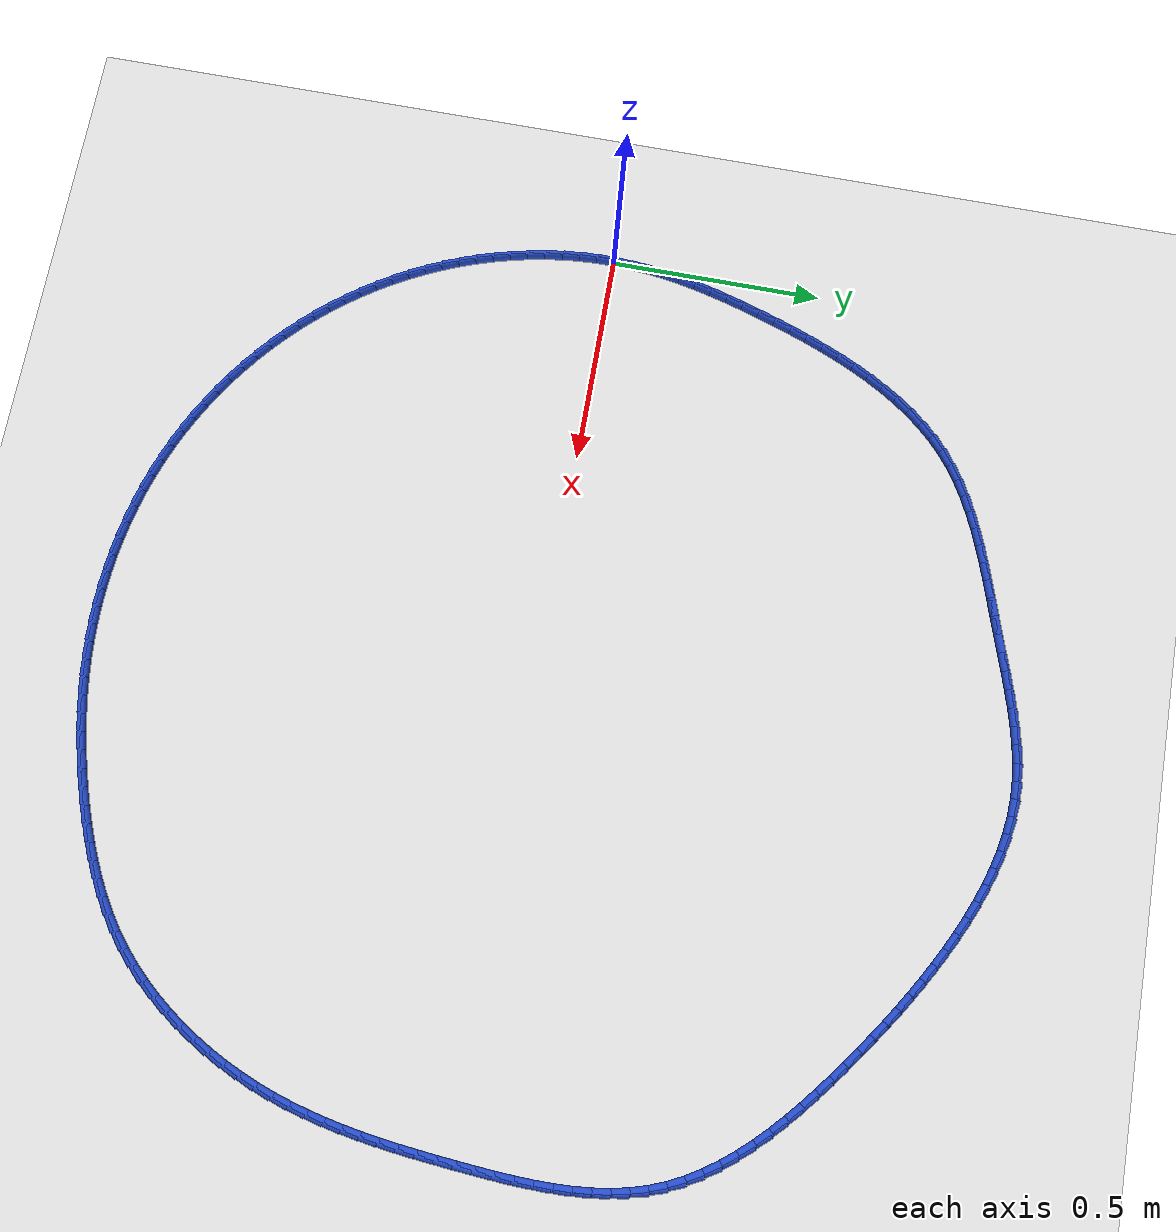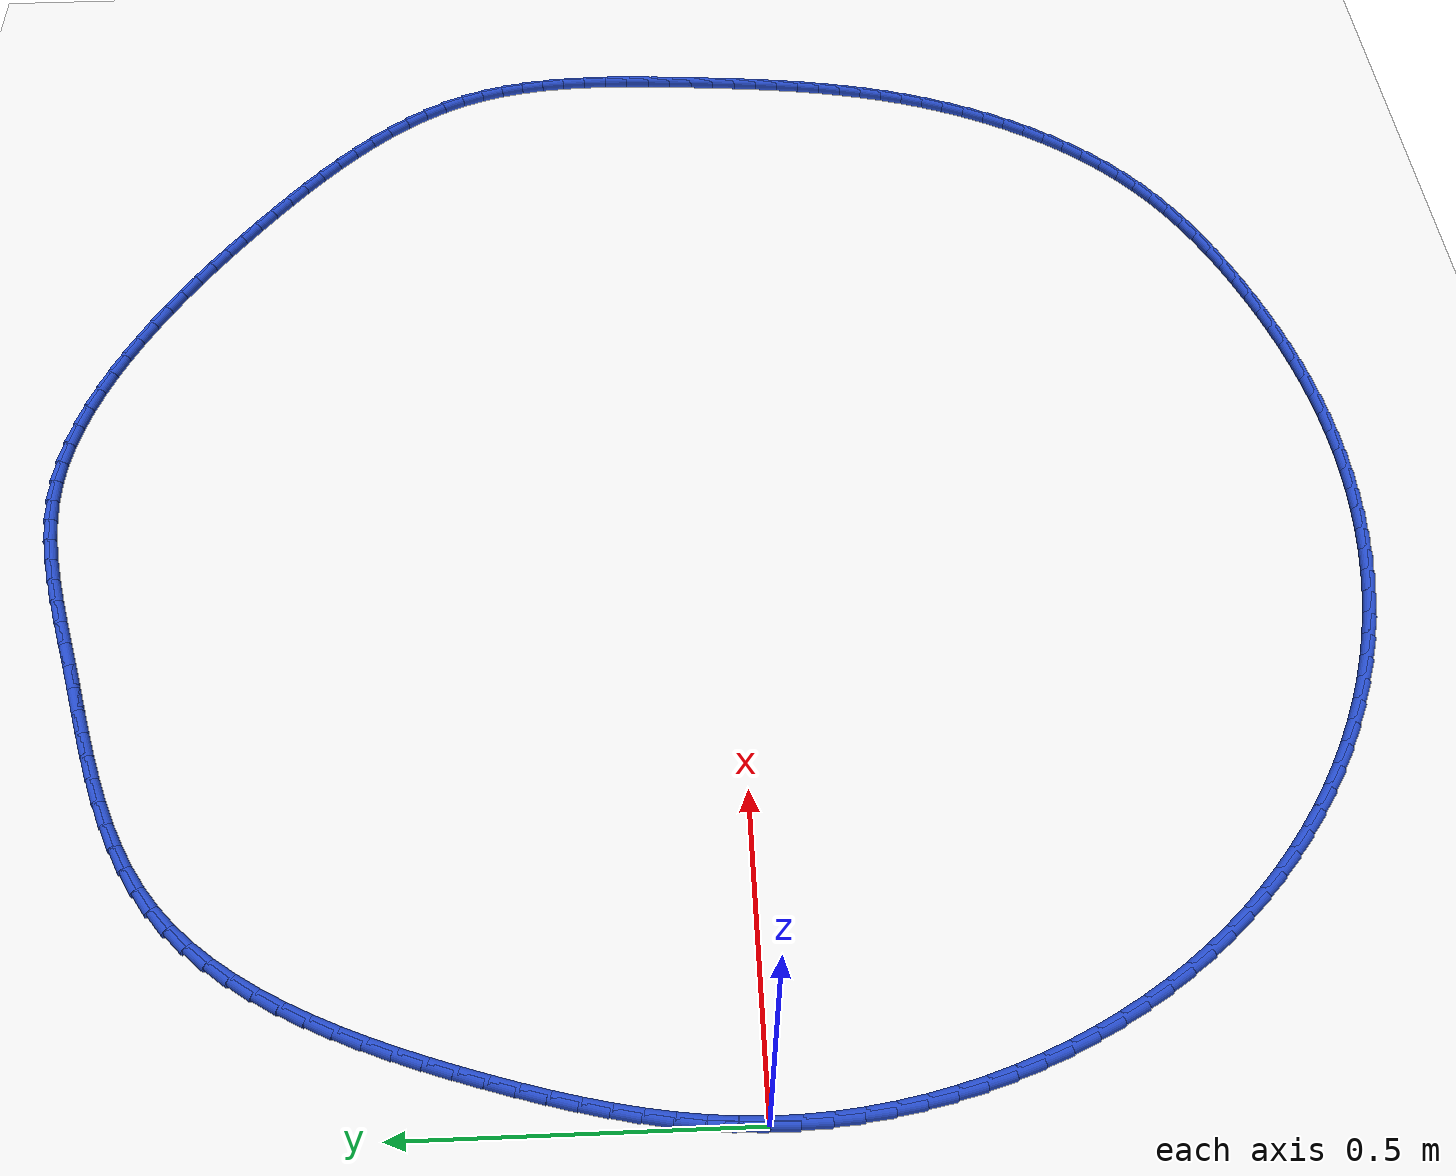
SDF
<sdf version="1.6">
 <world name="default">
  <light name="sun" type="directional">
   <pose>0 0 10 0 -0 0</pose>
   <diffuse>0.8 0.8 0.8 1</diffuse>
   <specular>0.2 0.2 0.2 1</specular>
   <attenuation>
    <range>1000</range>
    <constant>0.9</constant>
    <linear>0.01</linear>
    <quadratic>0.001</quadratic>
   </attenuation>
   <direction>-0.5 0.1 -0.9</direction>
  </light>
  <model name="ground_plane">
   <static>1</static>
   <link name="link">
    <collision name="collision">
     <geometry><plane><normal>0 0 1</normal><size>100 100</size></plane></geometry>
     <surface><friction><ode><mu>100</mu><mu2>50</mu2></ode></friction></surface>
    </collision>
    <visual name="visual">
     <cast_shadows>0</cast_shadows>
     <geometry><plane><normal>0 0 1</normal><size>100 100</size></plane></geometry>
     <material>
      <script><uri>file://media/materials/scripts/gazebo.material</uri><name>Gazebo/WhiteGlow</name></script>
     </material>
    </visual>
   </link>
  </model>
  <gravity>0 0 -9.8</gravity>
  <magnetic_field>6e-06 2.3e-05 -4.2e-05</magnetic_field>
  <atmosphere type="adiabatic"/>
  <physics name="default_physics" default="0" type="ode">
   <max_step_size>0.001</max_step_size>
   <real_time_factor>1</real_time_factor>
   <real_time_update_rate>1000</real_time_update_rate>
  </physics>
  <scene><ambient>0.4 0.4 0.4 1</ambient><background>0.7 0.7 0.7 1</background><shadows>1</shadows></scene>
  <spherical_coordinates>
   <surface_model>EARTH_WGS84</surface_model>
   <latitude_deg>0</latitude_deg>
   <longitude_deg>0</longitude_deg>
   <elevation>0</elevation>
   <heading_deg>0</heading_deg>
  </spherical_coordinates>
  <model name="line">
   <link name="link_0">
    <pose>-6.938893903907228e-17 5.551115123125783e-17 0.01 0 1.57 1.5295211178930346</pose>
    <collision name="collision">
     <geometry><cylinder><radius>0.01</radius><length>0.08</length></cylinder></geometry>
    </collision>
    <visual name="visual">
     <material>
      <script><name>Gazebo/Blue</name><uri>file://media/materials/scripts/gazebo.material</uri></script>
     </material>
     <geometry><cylinder><radius>0.01</radius><length>0.08</length></cylinder></geometry>
    </visual>
   </link>
   <link name="link_1">
    <pose>0.0016940753056678942 0.04102009919093619 0.01 0 1.57 1.4836181525590477</pose>
    <collision name="collision">
     <geometry><cylinder><radius>0.01</radius><length>0.08</length></cylinder></geometry>
    </collision>
    <visual name="visual">
     <material>
      <script><name>Gazebo/Blue</name><uri>file://media/materials/scripts/gazebo.material</uri></script>
     </material>
     <geometry><cylinder><radius>0.01</radius><length>0.08</length></cylinder></geometry>
    </visual>
   </link>
   <link name="link_2">
    <pose>0.00526283917718724 0.08185277789360729 0.01 0 1.57 1.441261052110527</pose>
    <collision name="collision">
     <geometry><cylinder><radius>0.01</radius><length>0.08</length></cylinder></geometry>
    </collision>
    <visual name="visual">
     <material>
      <script><name>Gazebo/Blue</name><uri>file://media/materials/scripts/gazebo.material</uri></script>
     </material>
     <geometry><cylinder><radius>0.01</radius><length>0.08</length></cylinder></geometry>
    </visual>
   </link>
   <link name="link_3">
    <pose>0.010562880971389308 0.12253949257791172 0.01 0 1.57 1.402671206864249</pose>
    <collision name="collision">
     <geometry><cylinder><radius>0.01</radius><length>0.08</length></cylinder></geometry>
    </collision>
    <visual name="visual">
     <material>
      <script><name>Gazebo/Blue</name><uri>file://media/materials/scripts/gazebo.material</uri></script>
     </material>
     <geometry><cylinder><radius>0.01</radius><length>0.08</length></cylinder></geometry>
    </visual>
   </link>
   <link name="link_4">
    <pose>0.01745079004510542 0.16312169971374776 0.01 0 1.57 1.3679834656666097</pose>
    <collision name="collision">
     <geometry><cylinder><radius>0.01</radius><length>0.08</length></cylinder></geometry>
    </collision>
    <visual name="visual">
     <material>
      <script><name>Gazebo/Blue</name><uri>file://media/materials/scripts/gazebo.material</uri></script>
     </material>
     <geometry><cylinder><radius>0.01</radius><length>0.08</length></cylinder></geometry>
    </visual>
   </link>
   <link name="link_5">
    <pose>0.02578315575516693 0.2036408557710138 0.01 0 1.57 1.3372603106143606</pose>
    <collision name="collision">
     <geometry><cylinder><radius>0.01</radius><length>0.08</length></cylinder></geometry>
    </collision>
    <visual name="visual">
     <material>
      <script><name>Gazebo/Blue</name><uri>file://media/materials/scripts/gazebo.material</uri></script>
     </material>
     <geometry><cylinder><radius>0.01</radius><length>0.08</length></cylinder></geometry>
    </visual>
   </link>
   <link name="link_6">
    <pose>0.03541656745840518 0.2441384172196081 0.01 0 1.57 1.3105073156449456</pose>
    <collision name="collision">
     <geometry><cylinder><radius>0.01</radius><length>0.08</length></cylinder></geometry>
    </collision>
    <visual name="visual">
     <material>
      <script><name>Gazebo/Blue</name><uri>file://media/materials/scripts/gazebo.material</uri></script>
     </material>
     <geometry><cylinder><radius>0.01</radius><length>0.08</length></cylinder></geometry>
    </visual>
   </link>
   <link name="link_7">
    <pose>0.04620761451165147 0.2846558405294289 0.01 0 1.57 1.2876881151883557</pose>
    <collision name="collision">
     <geometry><cylinder><radius>0.01</radius><length>0.08</length></cylinder></geometry>
    </collision>
    <visual name="visual">
     <material>
      <script><name>Gazebo/Blue</name><uri>file://media/materials/scripts/gazebo.material</uri></script>
     </material>
     <geometry><cylinder><radius>0.01</radius><length>0.08</length></cylinder></geometry>
    </visual>
   </link>
   <link name="link_8">
    <pose>0.05801288627173715 0.3252345821703746 0.01 0 1.57 1.2687377520558818</pose>
    <collision name="collision">
     <geometry><cylinder><radius>0.01</radius><length>0.08</length></cylinder></geometry>
    </collision>
    <visual name="visual">
     <material>
      <script><name>Gazebo/Blue</name><uri>file://media/materials/scripts/gazebo.material</uri></script>
     </material>
     <geometry><cylinder><radius>0.01</radius><length>0.08</length></cylinder></geometry>
    </visual>
   </link>
   <link name="link_9">
    <pose>0.07068897209549357 0.36591609861234353 0.01 0 1.57 1.2533195616153858</pose>
    <collision name="collision">
     <geometry><cylinder><radius>0.01</radius><length>0.08</length></cylinder></geometry>
    </collision>
    <visual name="visual">
     <material>
      <script><name>Gazebo/Blue</name><uri>file://media/materials/scripts/gazebo.material</uri></script>
     </material>
     <geometry><cylinder><radius>0.01</radius><length>0.08</length></cylinder></geometry>
    </visual>
   </link>
   <link name="link_10">
    <pose>0.08410109394157478 0.40673311828321956 0.01 0 1.57 1.2373657290991258</pose>
    <collision name="collision">
     <geometry><cylinder><radius>0.01</radius><length>0.08</length></cylinder></geometry>
    </collision>
    <visual name="visual">
     <material>
      <script><name>Gazebo/Blue</name><uri>file://media/materials/scripts/gazebo.material</uri></script>
     </material>
     <geometry><cylinder><radius>0.01</radius><length>0.08</length></cylinder></geometry>
    </visual>
   </link>
   <link name="link_11">
    <pose>0.09824954599700263 0.4475818040529693 0.01 0 1.57 1.217608481108015</pose>
    <collision name="collision">
     <geometry><cylinder><radius>0.01</radius><length>0.08</length></cylinder></geometry>
    </collision>
    <visual name="visual">
     <material>
      <script><name>Gazebo/Blue</name><uri>file://media/materials/scripts/gazebo.material</uri></script>
     </material>
     <geometry><cylinder><radius>0.01</radius><length>0.08</length></cylinder></geometry>
    </visual>
   </link>
   <link name="link_12">
    <pose>0.11324170555073036 0.48825005180185016 0.01 0 1.57 1.193781997664022</pose>
    <collision name="collision">
     <geometry><cylinder><radius>0.01</radius><length>0.08</length></cylinder></geometry>
    </collision>
    <visual name="visual">
     <material>
      <script><name>Gazebo/Blue</name><uri>file://media/materials/scripts/gazebo.material</uri></script>
     </material>
     <geometry><cylinder><radius>0.01</radius><length>0.08</length></cylinder></geometry>
    </visual>
   </link>
   <link name="link_13">
    <pose>0.12918788988161972 0.528522784916314 0.01 0 1.57 1.1656390461936397</pose>
    <collision name="collision">
     <geometry><cylinder><radius>0.01</radius><length>0.08</length></cylinder></geometry>
    </collision>
    <visual name="visual">
     <material>
      <script><name>Gazebo/Blue</name><uri>file://media/materials/scripts/gazebo.material</uri></script>
     </material>
     <geometry><cylinder><radius>0.01</radius><length>0.08</length></cylinder></geometry>
    </visual>
   </link>
   <link name="link_14">
    <pose>0.1461984162685323 0.5681849267828125 0.01 0 1.57 1.1328696306898038</pose>
    <collision name="collision">
     <geometry><cylinder><radius>0.01</radius><length>0.08</length></cylinder></geometry>
    </collision>
    <visual name="visual">
     <material>
      <script><name>Gazebo/Blue</name><uri>file://media/materials/scripts/gazebo.material</uri></script>
     </material>
     <geometry><cylinder><radius>0.01</radius><length>0.08</length></cylinder></geometry>
    </visual>
   </link>
   <link name="link_15">
    <pose>0.16438360199032978 0.6070214007877978 0.01 0 1.57 1.0951087397610708</pose>
    <collision name="collision">
     <geometry><cylinder><radius>0.01</radius><length>0.08</length></cylinder></geometry>
    </collision>
    <visual name="visual">
     <material>
      <script><name>Gazebo/Blue</name><uri>file://media/materials/scripts/gazebo.material</uri></script>
     </material>
     <geometry><cylinder><radius>0.01</radius><length>0.08</length></cylinder></geometry>
    </visual>
   </link>
   <link name="link_16">
    <pose>0.18385376432587386 0.6448171303177218 0.01 0 1.57 1.0519492333334464</pose>
    <collision name="collision">
     <geometry><cylinder><radius>0.01</radius><length>0.08</length></cylinder></geometry>
    </collision>
    <visual name="visual">
     <material>
      <script><name>Gazebo/Blue</name><uri>file://media/materials/scripts/gazebo.material</uri></script>
     </material>
     <geometry><cylinder><radius>0.01</radius><length>0.08</length></cylinder></geometry>
    </visual>
   </link>
   <link name="link_17">
    <pose>0.20471922055402605 0.6813570387590363 0.01 0 1.57 1.002963285717442</pose>
    <collision name="collision">
     <geometry><cylinder><radius>0.01</radius><length>0.08</length></cylinder></geometry>
    </collision>
    <visual name="visual">
     <material>
      <script><name>Gazebo/Blue</name><uri>file://media/materials/scripts/gazebo.material</uri></script>
     </material>
     <geometry><cylinder><radius>0.01</radius><length>0.08</length></cylinder></geometry>
    </visual>
   </link>
   <link name="link_18">
    <pose>0.22709028795364813 0.7164260494981931 0.01 0 1.57 0.9477364884585241</pose>
    <collision name="collision">
     <geometry><cylinder><radius>0.01</radius><length>0.08</length></cylinder></geometry>
    </collision>
    <visual name="visual">
     <material>
      <script><name>Gazebo/Blue</name><uri>file://media/materials/scripts/gazebo.material</uri></script>
     </material>
     <geometry><cylinder><radius>0.01</radius><length>0.08</length></cylinder></geometry>
    </visual>
   </link>
   <link name="link_19">
    <pose>0.2510772838036017 0.7498090859216442 0.01 0 1.57 0.8859188049033503</pose>
    <collision name="collision">
     <geometry><cylinder><radius>0.01</radius><length>0.08</length></cylinder></geometry>
    </collision>
    <visual name="visual">
     <material>
      <script><name>Gazebo/Blue</name><uri>file://media/materials/scripts/gazebo.material</uri></script>
     </material>
     <geometry><cylinder><radius>0.01</radius><length>0.08</length></cylinder></geometry>
    </visual>
   </link>
   <link name="link_20">
    <pose>0.2767905253827485 0.7812910714158415 0.01 0 1.57 0.8172951377439855</pose>
    <collision name="collision">
     <geometry><cylinder><radius>0.01</radius><length>0.08</length></cylinder></geometry>
    </collision>
    <visual name="visual">
     <material>
      <script><name>Gazebo/Blue</name><uri>file://media/materials/scripts/gazebo.material</uri></script>
     </material>
     <geometry><cylinder><radius>0.01</radius><length>0.08</length></cylinder></geometry>
    </visual>
   </link>
   <link name="link_21">
    <pose>0.30434032996995014 0.810656929367237 0.01 0 1.57 0.7418740528319384</pose>
    <collision name="collision">
     <geometry><cylinder><radius>0.01</radius><length>0.08</length></cylinder></geometry>
    </collision>
    <visual name="visual">
     <material>
      <script><name>Gazebo/Blue</name><uri>file://media/materials/scripts/gazebo.material</uri></script>
     </material>
     <geometry><cylinder><radius>0.01</radius><length>0.08</length></cylinder></geometry>
    </visual>
   </link>
   <link name="link_22">
    <pose>0.33383701484406814 0.8376915831622822 0.01 0 1.57 0.6610400251546933</pose>
    <collision name="collision">
     <geometry><cylinder><radius>0.01</radius><length>0.08</length></cylinder></geometry>
    </collision>
    <visual name="visual">
     <material>
      <script><name>Gazebo/Blue</name><uri>file://media/materials/scripts/gazebo.material</uri></script>
     </material>
     <geometry><cylinder><radius>0.01</radius><length>0.08</length></cylinder></geometry>
    </visual>
   </link>
   <link name="link_23">
    <pose>0.36536748216538006 0.8622151208831176 0.01 0 1.57 0.5845602938426694</pose>
    <collision name="collision">
     <geometry><cylinder><radius>0.01</radius><length>0.08</length></cylinder></geometry>
    </collision>
    <visual name="visual">
     <material>
      <script><name>Gazebo/Blue</name><uri>file://media/materials/scripts/gazebo.material</uri></script>
     </material>
     <geometry><cylinder><radius>0.01</radius><length>0.08</length></cylinder></geometry>
    </visual>
   </link>
   <link name="link_24">
    <pose>0.39881773146359645 0.8843493450722034 0.01 0 1.57 0.517694273193901</pose>
    <collision name="collision">
     <geometry><cylinder><radius>0.01</radius><length>0.08</length></cylinder></geometry>
    </collision>
    <visual name="visual">
     <material>
      <script><name>Gazebo/Blue</name><uri>file://media/materials/scripts/gazebo.material</uri></script>
     </material>
     <geometry><cylinder><radius>0.01</radius><length>0.08</length></cylinder></geometry>
    </visual>
   </link>
   <link name="link_25">
    <pose>0.43397153348185524 0.9043695848987165 0.01 0 1.57 0.4606440549411995</pose>
    <collision name="collision">
     <geometry><cylinder><radius>0.01</radius><length>0.08</length></cylinder></geometry>
    </collision>
    <visual name="visual">
     <material>
      <script><name>Gazebo/Blue</name><uri>file://media/materials/scripts/gazebo.material</uri></script>
     </material>
     <geometry><cylinder><radius>0.01</radius><length>0.08</length></cylinder></geometry>
    </visual>
   </link>
   <link name="link_26">
    <pose>0.4706118496830646 0.9225523849044123 0.01 0 1.57 0.413215427790466</pose>
    <collision name="collision">
     <geometry><cylinder><radius>0.01</radius><length>0.08</length></cylinder></geometry>
    </collision>
    <visual name="visual">
     <material>
      <script><name>Gazebo/Blue</name><uri>file://media/materials/scripts/gazebo.material</uri></script>
     </material>
     <geometry><cylinder><radius>0.01</radius><length>0.08</length></cylinder></geometry>
    </visual>
   </link>
   <link name="link_27">
    <pose>0.5085216415301321 0.9391742896310457 0.01 0 1.57 0.37502189391123536</pose>
    <collision name="collision">
     <geometry><cylinder><radius>0.01</radius><length>0.08</length></cylinder></geometry>
    </collision>
    <visual name="visual">
     <material>
      <script><name>Gazebo/Blue</name><uri>file://media/materials/scripts/gazebo.material</uri></script>
     </material>
     <geometry><cylinder><radius>0.01</radius><length>0.08</length></cylinder></geometry>
    </visual>
   </link>
   <link name="link_28">
    <pose>0.5474838704859656 0.9545118436203719 0.01 0 1.57 0.34561345637982777</pose>
    <collision name="collision">
     <geometry><cylinder><radius>0.01</radius><length>0.08</length></cylinder></geometry>
    </collision>
    <visual name="visual">
     <material>
      <script><name>Gazebo/Blue</name><uri>file://media/materials/scripts/gazebo.material</uri></script>
     </material>
     <geometry><cylinder><radius>0.01</radius><length>0.08</length></cylinder></geometry>
    </visual>
   </link>
   <link name="link_29">
    <pose>0.5872814980134727 0.9688415914141462 0.01 0 1.57 0.3245646430097049</pose>
    <collision name="collision">
     <geometry><cylinder><radius>0.01</radius><length>0.08</length></cylinder></geometry>
    </collision>
    <visual name="visual">
     <material>
      <script><name>Gazebo/Blue</name><uri>file://media/materials/scripts/gazebo.material</uri></script>
     </material>
     <geometry><cylinder><radius>0.01</radius><length>0.08</length></cylinder></geometry>
    </visual>
   </link>
   <link name="link_30">
    <pose>0.6276974855755613 0.9824400775541233 0.01 0 1.57 0.3115293324298856</pose>
    <collision name="collision">
     <geometry><cylinder><radius>0.01</radius><length>0.08</length></cylinder></geometry>
    </collision>
    <visual name="visual">
     <material>
      <script><name>Gazebo/Blue</name><uri>file://media/materials/scripts/gazebo.material</uri></script>
     </material>
     <geometry><cylinder><radius>0.01</radius><length>0.08</length></cylinder></geometry>
    </visual>
   </link>
   <link name="link_31">
    <pose>0.6685147946351391 0.9955838465820589 0.01 0 1.57 0.3062719283524712</pose>
    <collision name="collision">
     <geometry><cylinder><radius>0.01</radius><length>0.08</length></cylinder></geometry>
    </collision>
    <visual name="visual">
     <material>
      <script><name>Gazebo/Blue</name><uri>file://media/materials/scripts/gazebo.material</uri></script>
     </material>
     <geometry><cylinder><radius>0.01</radius><length>0.08</length></cylinder></geometry>
    </visual>
   </link>
   <link name="link_32">
    <pose>0.7095163866551143 1.008549443039708 0.01 0 1.57 0.30867940138229516</pose>
    <collision name="collision">
     <geometry><cylinder><radius>0.01</radius><length>0.08</length></cylinder></geometry>
    </collision>
    <visual name="visual">
     <material>
      <script><name>Gazebo/Blue</name><uri>file://media/materials/scripts/gazebo.material</uri></script>
     </material>
     <geometry><cylinder><radius>0.01</radius><length>0.08</length></cylinder></geometry>
    </visual>
   </link>
   <link name="link_33">
    <pose>0.7504852741185585 1.021613274740743 0.01 0 1.57 0.3149096828438092</pose>
    <collision name="collision">
     <geometry><cylinder><radius>0.01</radius><length>0.08</length></cylinder></geometry>
    </collision>
    <visual name="visual">
     <material>
      <script><name>Gazebo/Blue</name><uri>file://media/materials/scripts/gazebo.material</uri></script>
     </material>
     <geometry><cylinder><radius>0.01</radius><length>0.08</length></cylinder></geometry>
    </visual>
   </link>
   <link name="link_34">
    <pose>0.7912624325428919 1.0348964153355842 0.01 0 1.57 0.31370150610140723</pose>
    <collision name="collision">
     <geometry><cylinder><radius>0.01</radius><length>0.08</length></cylinder></geometry>
    </collision>
    <visual name="visual">
     <material>
      <script><name>Gazebo/Blue</name><uri>file://media/materials/scripts/gazebo.material</uri></script>
     </material>
     <geometry><cylinder><radius>0.01</radius><length>0.08</length></cylinder></geometry>
    </visual>
   </link>
   <link name="link_35">
    <pose>0.8318581429962248 1.0480662193699388 0.01 0 1.57 0.30286563058093263</pose>
    <collision name="collision">
     <geometry><cylinder><radius>0.01</radius><length>0.08</length></cylinder></geometry>
    </collision>
    <visual name="visual">
     <material>
      <script><name>Gazebo/Blue</name><uri>file://media/materials/scripts/gazebo.material</uri></script>
     </material>
     <geometry><cylinder><radius>0.01</radius><length>0.08</length></cylinder></geometry>
    </visual>
   </link>
   <link name="link_36">
    <pose>0.8723134334201893 1.0607076433590354 0.01 0 1.57 0.2821383303547089</pose>
    <collision name="collision">
     <geometry><cylinder><radius>0.01</radius><length>0.08</length></cylinder></geometry>
    </collision>
    <visual name="visual">
     <material>
      <script><name>Gazebo/Blue</name><uri>file://media/materials/scripts/gazebo.material</uri></script>
     </material>
     <geometry><cylinder><radius>0.01</radius><length>0.08</length></cylinder></geometry>
    </visual>
   </link>
   <link name="link_37">
    <pose>0.9126693317564154 1.0724056438181009 0.01 0 1.57 0.25116176876552576</pose>
    <collision name="collision">
     <geometry><cylinder><radius>0.01</radius><length>0.08</length></cylinder></geometry>
    </collision>
    <visual name="visual">
     <material>
      <script><name>Gazebo/Blue</name><uri>file://media/materials/scripts/gazebo.material</uri></script>
     </material>
     <geometry><cylinder><radius>0.01</radius><length>0.08</length></cylinder></geometry>
    </visual>
   </link>
   <link name="link_38">
    <pose>0.9529668659465347 1.0827451772623633 0.01 0 1.57 0.20953933117501528</pose>
    <collision name="collision">
     <geometry><cylinder><radius>0.01</radius><length>0.08</length></cylinder></geometry>
    </collision>
    <visual name="visual">
     <material>
      <script><name>Gazebo/Blue</name><uri>file://media/materials/scripts/gazebo.material</uri></script>
     </material>
     <geometry><cylinder><radius>0.01</radius><length>0.08</length></cylinder></geometry>
    </visual>
   </link>
   <link name="link_39">
    <pose>0.9932470639321782 1.0913112002070509 0.01 0 1.57 0.15693343383750571</pose>
    <collision name="collision">
     <geometry><cylinder><radius>0.01</radius><length>0.08</length></cylinder></geometry>
    </collision>
    <visual name="visual">
     <material>
      <script><name>Gazebo/Blue</name><uri>file://media/materials/scripts/gazebo.material</uri></script>
     </material>
     <geometry><cylinder><radius>0.01</radius><length>0.08</length></cylinder></geometry>
    </visual>
   </link>
   <link name="link_40">
    <pose>1.0335509536549763 1.097688669167391 0.01 0 1.57 0.09321437920420347</pose>
    <collision name="collision">
     <geometry><cylinder><radius>0.01</radius><length>0.08</length></cylinder></geometry>
    </collision>
    <visual name="visual">
     <material>
      <script><name>Gazebo/Blue</name><uri>file://media/materials/scripts/gazebo.material</uri></script>
     </material>
     <geometry><cylinder><radius>0.01</radius><length>0.08</length></cylinder></geometry>
    </visual>
   </link>
   <link name="link_41">
    <pose>1.0739195630565608 1.1014625406586114 0.01 0 1.57 0.018663360482117326</pose>
    <collision name="collision">
     <geometry><cylinder><radius>0.01</radius><length>0.08</length></cylinder></geometry>
    </collision>
    <visual name="visual">
     <material>
      <script><name>Gazebo/Blue</name><uri>file://media/materials/scripts/gazebo.material</uri></script>
     </material>
     <geometry><cylinder><radius>0.01</radius><length>0.08</length></cylinder></geometry>
    </visual>
   </link>
   <link name="link_42">
    <pose>1.1143938673068394 1.102218014906989 0.01 0 1.57 -0.061863083195858676</pose>
    <collision name="collision">
     <geometry><cylinder><radius>0.01</radius><length>0.08</length></cylinder></geometry>
    </collision>
    <visual name="visual">
     <material>
      <script><name>Gazebo/Blue</name><uri>file://media/materials/scripts/gazebo.material</uri></script>
     </material>
     <geometry><cylinder><radius>0.01</radius><length>0.08</length></cylinder></geometry>
    </visual>
   </link>
   <link name="link_43">
    <pose>1.1549793798032189 1.0997040621522185 0.01 0 1.57 -0.13672560935731223</pose>
    <collision name="collision">
     <geometry><cylinder><radius>0.01</radius><length>0.08</length></cylinder></geometry>
    </collision>
    <visual name="visual">
     <material>
      <script><name>Gazebo/Blue</name><uri>file://media/materials/scripts/gazebo.material</uri></script>
     </material>
     <geometry><cylinder><radius>0.01</radius><length>0.08</length></cylinder></geometry>
    </visual>
   </link>
   <link name="link_44">
    <pose>1.1955846558857024 1.0941174255805108 0.01 0 1.57 -0.2041098291954975</pose>
    <collision name="collision">
     <geometry><cylinder><radius>0.01</radius><length>0.08</length></cylinder></geometry>
    </collision>
    <visual name="visual">
     <material>
      <script><name>Gazebo/Blue</name><uri>file://media/materials/scripts/gazebo.material</uri></script>
     </material>
     <geometry><cylinder><radius>0.01</radius><length>0.08</length></cylinder></geometry>
    </visual>
   </link>
   <link name="link_45">
    <pose>1.2361018305565772 1.0857306809927072 0.01 0 1.57 -0.264348575901726</pose>
    <collision name="collision">
     <geometry><cylinder><radius>0.01</radius><length>0.08</length></cylinder></geometry>
    </collision>
    <visual name="visual">
     <material>
      <script><name>Gazebo/Blue</name><uri>file://media/materials/scripts/gazebo.material</uri></script>
     </material>
     <geometry><cylinder><radius>0.01</radius><length>0.08</length></cylinder></geometry>
    </visual>
   </link>
   <link name="link_46">
    <pose>1.2764230388181306 1.0748164041896482 0.01 0 1.57 -0.3179247812549229</pose>
    <collision name="collision">
     <geometry><cylinder><radius>0.01</radius><length>0.08</length></cylinder></geometry>
    </collision>
    <visual name="visual">
     <material>
      <script><name>Gazebo/Blue</name><uri>file://media/materials/scripts/gazebo.material</uri></script>
     </material>
     <geometry><cylinder><radius>0.01</radius><length>0.08</length></cylinder></geometry>
    </visual>
   </link>
   <link name="link_47">
    <pose>1.3164404156726492 1.061647170972174 0.01 0 1.57 -0.3653835118112259</pose>
    <collision name="collision">
     <geometry><cylinder><radius>0.01</radius><length>0.08</length></cylinder></geometry>
    </collision>
    <visual name="visual">
     <material>
      <script><name>Gazebo/Blue</name><uri>file://media/materials/scripts/gazebo.material</uri></script>
     </material>
     <geometry><cylinder><radius>0.01</radius><length>0.08</length></cylinder></geometry>
    </visual>
   </link>
   <link name="link_48">
    <pose>1.356046096122421 1.0464955571411256 0.01 0 1.57 -0.4072718067524072</pose>
    <collision name="collision">
     <geometry><cylinder><radius>0.01</radius><length>0.08</length></cylinder></geometry>
    </collision>
    <visual name="visual">
     <material>
      <script><name>Gazebo/Blue</name><uri>file://media/materials/scripts/gazebo.material</uri></script>
     </material>
     <geometry><cylinder><radius>0.01</radius><length>0.08</length></cylinder></geometry>
    </visual>
   </link>
   <link name="link_49">
    <pose>1.3951322151697316 1.029634138497343 0.01 0 1.57 -0.4441008981339359</pose>
    <collision name="collision">
     <geometry><cylinder><radius>0.01</radius><length>0.08</length></cylinder></geometry>
    </collision>
    <visual name="visual">
     <material>
      <script><name>Gazebo/Blue</name><uri>file://media/materials/scripts/gazebo.material</uri></script>
     </material>
     <geometry><cylinder><radius>0.01</radius><length>0.08</length></cylinder></geometry>
    </visual>
   </link>
   <link name="link_50">
    <pose>1.4335909078168685 1.0113354908416672 0.01 0 1.57 -0.4763241944336851</pose>
    <collision name="collision">
     <geometry><cylinder><radius>0.01</radius><length>0.08</length></cylinder></geometry>
    </collision>
    <visual name="visual">
     <material>
      <script><name>Gazebo/Blue</name><uri>file://media/materials/scripts/gazebo.material</uri></script>
     </material>
     <geometry><cylinder><radius>0.01</radius><length>0.08</length></cylinder></geometry>
    </visual>
   </link>
   <link name="link_51">
    <pose>1.47131430906612 0.9918721899749388 0.01 0 1.57 -0.5043252182486192</pose>
    <collision name="collision">
     <geometry><cylinder><radius>0.01</radius><length>0.08</length></cylinder></geometry>
    </collision>
    <visual name="visual">
     <material>
      <script><name>Gazebo/Blue</name><uri>file://media/materials/scripts/gazebo.material</uri></script>
     </material>
     <geometry><cylinder><radius>0.01</radius><length>0.08</length></cylinder></geometry>
    </visual>
   </link>
   <link name="link_52">
    <pose>1.5081945640054275 0.9715168011389465 0.01 0 1.57 -0.5289346034649841</pose>
    <collision name="collision">
     <geometry><cylinder><radius>0.01</radius><length>0.08</length></cylinder></geometry>
    </collision>
    <visual name="visual">
     <material>
      <script><name>Gazebo/Blue</name><uri>file://media/materials/scripts/gazebo.material</uri></script>
     </material>
     <geometry><cylinder><radius>0.01</radius><length>0.08</length></cylinder></geometry>
    </visual>
   </link>
   <link name="link_53">
    <pose>1.5441784429977714 0.950484700328986 0.01 0 1.57 -0.5519147126262431</pose>
    <collision name="collision">
     <geometry><cylinder><radius>0.01</radius><length>0.08</length></cylinder></geometry>
    </collision>
    <visual name="visual">
     <material>
      <script><name>Gazebo/Blue</name><uri>file://media/materials/scripts/gazebo.material</uri></script>
     </material>
     <geometry><cylinder><radius>0.01</radius><length>0.08</length></cylinder></geometry>
    </visual>
   </link>
   <link name="link_54">
    <pose>1.579395147887068 0.9288002691897533 0.01 0 1.57 -0.5733495858450668</pose>
    <collision name="collision">
     <geometry><cylinder><radius>0.01</radius><length>0.08</length></cylinder></geometry>
    </collision>
    <visual name="visual">
     <material>
      <script><name>Gazebo/Blue</name><uri>file://media/materials/scripts/gazebo.material</uri></script>
     </material>
     <geometry><cylinder><radius>0.01</radius><length>0.08</length></cylinder></geometry>
    </visual>
   </link>
   <link name="link_55">
    <pose>1.6140119192119413 0.9064480652316694 0.01 0 1.57 -0.5929688252541696</pose>
    <collision name="collision">
     <geometry><cylinder><radius>0.01</radius><length>0.08</length></cylinder></geometry>
    </collision>
    <visual name="visual">
     <material>
      <script><name>Gazebo/Blue</name><uri>file://media/materials/scripts/gazebo.material</uri></script>
     </material>
     <geometry><cylinder><radius>0.01</radius><length>0.08</length></cylinder></geometry>
    </visual>
   </link>
   <link name="link_56">
    <pose>1.648195997511015 0.8834126459651539 0.01 0 1.57 -0.610548632824417</pose>
    <collision name="collision">
     <geometry><cylinder><radius>0.01</radius><length>0.08</length></cylinder></geometry>
    </collision>
    <visual name="visual">
     <material>
      <script><name>Gazebo/Blue</name><uri>file://media/materials/scripts/gazebo.material</uri></script>
     </material>
     <geometry><cylinder><radius>0.01</radius><length>0.08</length></cylinder></geometry>
    </visual>
   </link>
   <link name="link_57">
    <pose>1.682114623322912 0.859678568900628 0.01 0 1.57 -0.625918684527478</pose>
    <collision name="collision">
     <geometry><cylinder><radius>0.01</radius><length>0.08</length></cylinder></geometry>
    </collision>
    <visual name="visual">
     <material>
      <script><name>Gazebo/Blue</name><uri>file://media/materials/scripts/gazebo.material</uri></script>
     </material>
     <geometry><cylinder><radius>0.01</radius><length>0.08</length></cylinder></geometry>
    </visual>
   </link>
   <link name="link_58">
    <pose>1.7159350371862565 0.8352303915485114 0.01 0 1.57 -0.6391139453068592</pose>
    <collision name="collision">
     <geometry><cylinder><radius>0.01</radius><length>0.08</length></cylinder></geometry>
    </collision>
    <visual name="visual">
     <material>
      <script><name>Gazebo/Blue</name><uri>file://media/materials/scripts/gazebo.material</uri></script>
     </material>
     <geometry><cylinder><radius>0.01</radius><length>0.08</length></cylinder></geometry>
    </visual>
   </link>
   <link name="link_59">
    <pose>1.7498148541892842 0.8100520128253015 0.01 0 1.57 -0.6534657975726278</pose>
    <collision name="collision">
     <geometry><cylinder><radius>0.01</radius><length>0.08</length></cylinder></geometry>
    </collision>
    <visual name="visual">
     <material>
      <script><name>Gazebo/Blue</name><uri>file://media/materials/scripts/gazebo.material</uri></script>
     </material>
     <geometry><cylinder><radius>0.01</radius><length>0.08</length></cylinder></geometry>
    </visual>
   </link>
   <link name="link_60">
    <pose>1.7836924828760274 0.7841123330664211 0.01 0 1.57 -0.6723828446860911</pose>
    <collision name="collision">
     <geometry><cylinder><radius>0.01</radius><length>0.08</length></cylinder></geometry>
    </collision>
    <visual name="visual">
     <material>
      <script><name>Gazebo/Blue</name><uri>file://media/materials/scripts/gazebo.material</uri></script>
     </material>
     <geometry><cylinder><radius>0.01</radius><length>0.08</length></cylinder></geometry>
    </visual>
   </link>
   <link name="link_61">
    <pose>1.817288328909489 0.7573653363834301 0.01 0 1.57 -0.6961674003247227</pose>
    <collision name="collision">
     <geometry><cylinder><radius>0.01</radius><length>0.08</length></cylinder></geometry>
    </collision>
    <visual name="visual">
     <material>
      <script><name>Gazebo/Blue</name><uri>file://media/materials/scripts/gazebo.material</uri></script>
     </material>
     <geometry><cylinder><radius>0.01</radius><length>0.08</length></cylinder></geometry>
    </visual>
   </link>
   <link name="link_62">
    <pose>1.8503134132372085 0.7297643647655644 0.01 0 1.57 -0.7250803979246387</pose>
    <collision name="collision">
     <geometry><cylinder><radius>0.01</radius><length>0.08</length></cylinder></geometry>
    </collision>
    <visual name="visual">
     <material>
      <script><name>Gazebo/Blue</name><uri>file://media/materials/scripts/gazebo.material</uri></script>
     </material>
     <geometry><cylinder><radius>0.01</radius><length>0.08</length></cylinder></geometry>
    </visual>
   </link>
   <link name="link_63">
    <pose>1.8824787568067263 0.7012627602020596 0.01 0 1.57 -0.7594763305677511</pose>
    <collision name="collision">
     <geometry><cylinder><radius>0.01</radius><length>0.08</length></cylinder></geometry>
    </collision>
    <visual name="visual">
     <material>
      <script><name>Gazebo/Blue</name><uri>file://media/materials/scripts/gazebo.material</uri></script>
     </material>
     <geometry><cylinder><radius>0.01</radius><length>0.08</length></cylinder></geometry>
    </visual>
   </link>
   <link name="link_64">
    <pose>1.9134953805655814 0.6718138646821517 0.01 0 1.57 -0.7997906071380042</pose>
    <collision name="collision">
     <geometry><cylinder><radius>0.01</radius><length>0.08</length></cylinder></geometry>
    </collision>
    <visual name="visual">
     <material>
      <script><name>Gazebo/Blue</name><uri>file://media/materials/scripts/gazebo.material</uri></script>
     </material>
     <geometry><cylinder><radius>0.01</radius><length>0.08</length></cylinder></geometry>
    </visual>
   </link>
   <link name="link_65">
    <pose>1.943074305461313 0.6413710201950757 0.01 0 1.57 -0.8465195726522055</pose>
    <collision name="collision">
     <geometry><cylinder><radius>0.01</radius><length>0.08</length></cylinder></geometry>
    </collision>
    <visual name="visual">
     <material>
      <script><name>Gazebo/Blue</name><uri>file://media/materials/scripts/gazebo.material</uri></script>
     </material>
     <geometry><cylinder><radius>0.01</radius><length>0.08</length></cylinder></geometry>
    </visual>
   </link>
   <link name="link_66">
    <pose>1.9709265524414619 0.6098875687300676 0.01 0 1.57 -0.9001872768823145</pose>
    <collision name="collision">
     <geometry><cylinder><radius>0.01</radius><length>0.08</length></cylinder></geometry>
    </collision>
    <visual name="visual">
     <material>
      <script><name>Gazebo/Blue</name><uri>file://media/materials/scripts/gazebo.material</uri></script>
     </material>
     <geometry><cylinder><radius>0.01</radius><length>0.08</length></cylinder></geometry>
    </visual>
   </link>
   <link name="link_67">
    <pose>1.9967631424535661 0.577316852276363 0.01 0 1.57 -0.9612919098532383</pose>
    <collision name="collision">
     <geometry><cylinder><radius>0.01</radius><length>0.08</length></cylinder></geometry>
    </collision>
    <visual name="visual">
     <material>
      <script><name>Gazebo/Blue</name><uri>file://media/materials/scripts/gazebo.material</uri></script>
     </material>
     <geometry><cylinder><radius>0.01</radius><length>0.08</length></cylinder></geometry>
    </visual>
   </link>
   <link name="link_68">
    <pose>2.0202950964451665 0.5436122128231973 0.01 0 1.57 -1.0302249422182974</pose>
    <collision name="collision">
     <geometry><cylinder><radius>0.01</radius><length>0.08</length></cylinder></geometry>
    </collision>
    <visual name="visual">
     <material>
      <script><name>Gazebo/Blue</name><uri>file://media/materials/scripts/gazebo.material</uri></script>
     </material>
     <geometry><cylinder><radius>0.01</radius><length>0.08</length></cylinder></geometry>
    </visual>
   </link>
   <link name="link_69">
    <pose>2.041233435363802 0.5087269923598067 0.01 0 1.57 -1.1071594609357402</pose>
    <collision name="collision">
     <geometry><cylinder><radius>0.01</radius><length>0.08</length></cylinder></geometry>
    </collision>
    <visual name="visual">
     <material>
      <script><name>Gazebo/Blue</name><uri>file://media/materials/scripts/gazebo.material</uri></script>
     </material>
     <geometry><cylinder><radius>0.01</radius><length>0.08</length></cylinder></geometry>
    </visual>
   </link>
   <link name="link_70">
    <pose>2.0592891801570126 0.47261453287542643 0.01 0 1.57 -1.191651830527927</pose>
    <collision name="collision">
     <geometry><cylinder><radius>0.01</radius><length>0.08</length></cylinder></geometry>
    </collision>
    <visual name="visual">
     <material>
      <script><name>Gazebo/Blue</name><uri>file://media/materials/scripts/gazebo.material</uri></script>
     </material>
     <geometry><cylinder><radius>0.01</radius><length>0.08</length></cylinder></geometry>
    </visual>
   </link>
   <link name="link_71">
    <pose>2.074183337322672 0.435231577977146 0.01 0 1.57 -1.2758939323515583</pose>
    <collision name="collision">
     <geometry><cylinder><radius>0.01</radius><length>0.08</length></cylinder></geometry>
    </collision>
    <visual name="visual">
     <material>
      <script><name>Gazebo/Blue</name><uri>file://media/materials/scripts/gazebo.material</uri></script>
     </material>
     <geometry><cylinder><radius>0.01</radius><length>0.08</length></cylinder></geometry>
    </visual>
   </link>
   <link name="link_72">
    <pose>2.0859096153082564 0.39662776828719015 0.01 0 1.57 -1.351290595813787</pose>
    <collision name="collision">
     <geometry><cylinder><radius>0.01</radius><length>0.08</length></cylinder></geometry>
    </collision>
    <visual name="visual">
     <material>
      <script><name>Gazebo/Blue</name><uri>file://media/materials/scripts/gazebo.material</uri></script>
     </material>
     <geometry><cylinder><radius>0.01</radius><length>0.08</length></cylinder></geometry>
    </visual>
   </link>
   <link name="link_73">
    <pose>2.0947607190092348 0.3569545987694727 0.01 0 1.57 -1.4171863393546058</pose>
    <collision name="collision">
     <geometry><cylinder><radius>0.01</radius><length>0.08</length></cylinder></geometry>
    </collision>
    <visual name="visual">
     <material>
      <script><name>Gazebo/Blue</name><uri>file://media/materials/scripts/gazebo.material</uri></script>
     </material>
     <geometry><cylinder><radius>0.01</radius><length>0.08</length></cylinder></geometry>
    </visual>
   </link>
   <link name="link_74">
    <pose>2.1010446117442947 0.31636876223110305 0.01 0 1.57 -1.4737516445435916</pose>
    <collision name="collision">
     <geometry><cylinder><radius>0.01</radius><length>0.08</length></cylinder></geometry>
    </collision>
    <visual name="visual">
     <material>
      <script><name>Gazebo/Blue</name><uri>file://media/materials/scripts/gazebo.material</uri></script>
     </material>
     <geometry><cylinder><radius>0.01</radius><length>0.08</length></cylinder></geometry>
    </visual>
   </link>
   <link name="link_75">
    <pose>2.1050692568321243 0.2750269514791898 0.01 0 1.57 -1.521401469692525</pose>
    <collision name="collision">
     <geometry><cylinder><radius>0.01</radius><length>0.08</length></cylinder></geometry>
    </collision>
    <visual name="visual">
     <material>
      <script><name>Gazebo/Blue</name><uri>file://media/materials/scripts/gazebo.material</uri></script>
     </material>
     <geometry><cylinder><radius>0.01</radius><length>0.08</length></cylinder></geometry>
    </visual>
   </link>
   <link name="link_76">
    <pose>2.1071426175914123 0.23308585932084142 0.01 0 1.57 -1.5606503228294806</pose>
    <collision name="collision">
     <geometry><cylinder><radius>0.01</radius><length>0.08</length></cylinder></geometry>
    </collision>
    <visual name="visual">
     <material>
      <script><name>Gazebo/Blue</name><uri>file://media/materials/scripts/gazebo.material</uri></script>
     </material>
     <geometry><cylinder><radius>0.01</radius><length>0.08</length></cylinder></geometry>
    </visual>
   </link>
   <link name="link_77">
    <pose>2.1075726573408473 0.1907021785631674 0.01 0 1.57 1.5495825673429766</pose>
    <collision name="collision">
     <geometry><cylinder><radius>0.01</radius><length>0.08</length></cylinder></geometry>
    </collision>
    <visual name="visual">
     <material>
      <script><name>Gazebo/Blue</name><uri>file://media/materials/scripts/gazebo.material</uri></script>
     </material>
     <geometry><cylinder><radius>0.01</radius><length>0.08</length></cylinder></geometry>
    </visual>
   </link>
   <link name="link_78">
    <pose>2.106667339399118 0.14803260201327595 0.01 0 1.57 1.5256688681260615</pose>
    <collision name="collision">
     <geometry><cylinder><radius>0.01</radius><length>0.08</length></cylinder></geometry>
    </collision>
    <visual name="visual">
     <material>
      <script><name>Gazebo/Blue</name><uri>file://media/materials/scripts/gazebo.material</uri></script>
     </material>
     <geometry><cylinder><radius>0.01</radius><length>0.08</length></cylinder></geometry>
    </visual>
   </link>
   <link name="link_79">
    <pose>2.1047346270849125 0.10523382247827656 0.01 0 1.57 1.5088680544122581</pose>
    <collision name="collision">
     <geometry><cylinder><radius>0.01</radius><length>0.08</length></cylinder></geometry>
    </collision>
    <visual name="visual">
     <material>
      <script><name>Gazebo/Blue</name><uri>file://media/materials/scripts/gazebo.material</uri></script>
     </material>
     <geometry><cylinder><radius>0.01</radius><length>0.08</length></cylinder></geometry>
    </visual>
   </link>
   <link name="link_80">
    <pose>2.1020824837169187 0.06246253276527768 0.01 0 1.57 1.498958215360049</pose>
    <collision name="collision">
     <geometry><cylinder><radius>0.01</radius><length>0.08</length></cylinder></geometry>
    </collision>
    <visual name="visual">
     <material>
      <script><name>Gazebo/Blue</name><uri>file://media/materials/scripts/gazebo.material</uri></script>
     </material>
     <geometry><cylinder><radius>0.01</radius><length>0.08</length></cylinder></geometry>
    </visual>
   </link>
   <link name="link_81">
    <pose>2.0990178060190656 0.019875055912803596 0.01 0 1.57 1.4926832107745691</pose>
    <collision name="collision">
     <geometry><cylinder><radius>0.01</radius><length>0.08</length></cylinder></geometry>
    </collision>
    <visual name="visual">
     <material>
      <script><name>Gazebo/Blue</name><uri>file://media/materials/scripts/gazebo.material</uri></script>
     </material>
     <geometry><cylinder><radius>0.01</radius><length>0.08</length></cylinder></geometry>
    </visual>
   </link>
   <link name="link_82">
    <pose>2.0957071992923137 -0.022420921470128787 0.01 0 1.57 1.4836548767339648</pose>
    <collision name="collision">
     <geometry><cylinder><radius>0.01</radius><length>0.08</length></cylinder></geometry>
    </collision>
    <visual name="visual">
     <material>
      <script><name>Gazebo/Blue</name><uri>file://media/materials/scripts/gazebo.material</uri></script>
     </material>
     <geometry><cylinder><radius>0.01</radius><length>0.08</length></cylinder></geometry>
    </visual>
   </link>
   <link name="link_83">
    <pose>2.092038540830168 -0.06441434259548094 0.01 0 1.57 1.4710652988678214</pose>
    <collision name="collision">
     <geometry><cylinder><radius>0.01</radius><length>0.08</length></cylinder></geometry>
    </collision>
    <visual name="visual">
     <material>
      <script><name>Gazebo/Blue</name><uri>file://media/materials/scripts/gazebo.material</uri></script>
     </material>
     <geometry><cylinder><radius>0.01</radius><length>0.08</length></cylinder></geometry>
    </visual>
   </link>
   <link name="link_84">
    <pose>2.087866792371639 -0.10610556188633669 0.01 0 1.57 1.454866451488957</pose>
    <collision name="collision">
     <geometry><cylinder><radius>0.01</radius><length>0.08</length></cylinder></geometry>
    </collision>
    <visual name="visual">
     <material>
      <script><name>Gazebo/Blue</name><uri>file://media/materials/scripts/gazebo.material</uri></script>
     </material>
     <geometry><cylinder><radius>0.01</radius><length>0.08</length></cylinder></geometry>
    </visual>
   </link>
   <link name="link_85">
    <pose>2.0830469156557374 -0.14749493376577896 0.01 0 1.57 1.4350260833197779</pose>
    <collision name="collision">
     <geometry><cylinder><radius>0.01</radius><length>0.08</length></cylinder></geometry>
    </collision>
    <visual name="visual">
     <material>
      <script><name>Gazebo/Blue</name><uri>file://media/materials/scripts/gazebo.material</uri></script>
     </material>
     <geometry><cylinder><radius>0.01</radius><length>0.08</length></cylinder></geometry>
    </visual>
   </link>
   <link name="link_86">
    <pose>2.0774338724214747 -0.1885828126568909 0.01 0 1.57 1.4115346442727235</pose>
    <collision name="collision">
     <geometry><cylinder><radius>0.01</radius><length>0.08</length></cylinder></geometry>
    </collision>
    <visual name="visual">
     <material>
      <script><name>Gazebo/Blue</name><uri>file://media/materials/scripts/gazebo.material</uri></script>
     </material>
     <geometry><cylinder><radius>0.01</radius><length>0.08</length></cylinder></geometry>
    </visual>
   </link>
   <link name="link_87">
    <pose>2.0708826244078598 -0.22936955298275613 0.01 0 1.57 1.3844136220203782</pose>
    <collision name="collision">
     <geometry><cylinder><radius>0.01</radius><length>0.08</length></cylinder></geometry>
    </collision>
    <visual name="visual">
     <material>
      <script><name>Gazebo/Blue</name><uri>file://media/materials/scripts/gazebo.material</uri></script>
     </material>
     <geometry><cylinder><radius>0.01</radius><length>0.08</length></cylinder></geometry>
    </visual>
   </link>
   <link name="link_88">
    <pose>2.063248133353905 -0.26985550916645623 0.01 0 1.57 1.3537249263923825</pose>
    <collision name="collision">
     <geometry><cylinder><radius>0.01</radius><length>0.08</length></cylinder></geometry>
    </collision>
    <visual name="visual">
     <material>
      <script><name>Gazebo/Blue</name><uri>file://media/materials/scripts/gazebo.material</uri></script>
     </material>
     <geometry><cylinder><radius>0.01</radius><length>0.08</length></cylinder></geometry>
    </visual>
   </link>
   <link name="link_89">
    <pose>2.0543853609986216 -0.310041035631075 0.01 0 1.57 1.3195806752709096</pose>
    <collision name="collision">
     <geometry><cylinder><radius>0.01</radius><length>0.08</length></cylinder></geometry>
    </collision>
    <visual name="visual">
     <material>
      <script><name>Gazebo/Blue</name><uri>file://media/materials/scripts/gazebo.material</uri></script>
     </material>
     <geometry><cylinder><radius>0.01</radius><length>0.08</length></cylinder></geometry>
    </visual>
   </link>
   <link name="link_90">
    <pose>2.044149269081018 -0.3499264867996954 0.01 0 1.57 1.2821524114344396</pose>
    <collision name="collision">
     <geometry><cylinder><radius>0.01</radius><length>0.08</length></cylinder></geometry>
    </collision>
    <visual name="visual">
     <material>
      <script><name>Gazebo/Blue</name><uri>file://media/materials/scripts/gazebo.material</uri></script>
     </material>
     <geometry><cylinder><radius>0.01</radius><length>0.08</length></cylinder></geometry>
    </visual>
   </link>
   <link name="link_91">
    <pose>2.032394819340106 -0.3895122170954004 0.01 0 1.57 1.241680064681204</pose>
    <collision name="collision">
     <geometry><cylinder><radius>0.01</radius><length>0.08</length></cylinder></geometry>
    </collision>
    <visual name="visual">
     <material>
      <script><name>Gazebo/Blue</name><uri>file://media/materials/scripts/gazebo.material</uri></script>
     </material>
     <geometry><cylinder><radius>0.01</radius><length>0.08</length></cylinder></geometry>
    </visual>
   </link>
   <link name="link_92">
    <pose>2.0189770824673055 -0.4287984660180517 0.01 0 1.57 1.1990178574637749</pose>
    <collision name="collision">
     <geometry><cylinder><radius>0.01</radius><length>0.08</length></cylinder></geometry>
    </collision>
    <visual name="visual">
     <material>
      <script><name>Gazebo/Blue</name><uri>file://media/materials/scripts/gazebo.material</uri></script>
     </material>
     <geometry><cylinder><radius>0.01</radius><length>0.08</length></cylinder></geometry>
    </visual>
   </link>
   <link name="link_93">
    <pose>2.003792755313101 -0.4677415657101033 0.01 0 1.57 1.1555575199309271</pose>
    <collision name="collision">
     <geometry><cylinder><radius>0.01</radius><length>0.08</length></cylinder></geometry>
    </collision>
    <visual name="visual">
     <material>
      <script><name>Gazebo/Blue</name><uri>file://media/materials/scripts/gazebo.material</uri></script>
     </material>
     <geometry><cylinder><radius>0.01</radius><length>0.08</length></cylinder></geometry>
    </visual>
   </link>
   <link name="link_94">
    <pose>1.9868427681966372 -0.5061879026388773 0.01 0 1.57 1.1111982553909383</pose>
    <collision name="collision">
     <geometry><cylinder><radius>0.01</radius><length>0.08</length></cylinder></geometry>
    </collision>
    <visual name="visual">
     <material>
      <script><name>Gazebo/Blue</name><uri>file://media/materials/scripts/gazebo.material</uri></script>
     </material>
     <geometry><cylinder><radius>0.01</radius><length>0.08</length></cylinder></geometry>
    </visual>
   </link>
   <link name="link_95">
    <pose>1.9681441021813377 -0.5439669329139194 0.01 0 1.57 1.0656135610040476</pose>
    <collision name="collision">
     <geometry><cylinder><radius>0.01</radius><length>0.08</length></cylinder></geometry>
    </collision>
    <visual name="visual">
     <material>
      <script><name>Gazebo/Blue</name><uri>file://media/materials/scripts/gazebo.material</uri></script>
     </material>
     <geometry><cylinder><radius>0.01</radius><length>0.08</length></cylinder></geometry>
    </visual>
   </link>
   <link name="link_96">
    <pose>1.9477137383306284 -0.5809081126447766 0.01 0 1.57 1.0184836160174242</pose>
    <collision name="collision">
     <geometry><cylinder><radius>0.01</radius><length>0.08</length></cylinder></geometry>
    </collision>
    <visual name="visual">
     <material>
      <script><name>Gazebo/Blue</name><uri>file://media/materials/scripts/gazebo.material</uri></script>
     </material>
     <geometry><cylinder><radius>0.01</radius><length>0.08</length></cylinder></geometry>
    </visual>
   </link>
   <link name="link_97">
    <pose>1.9255686577079347 -0.6168408979409933 0.01 0 1.57 0.9694954440958722</pose>
    <collision name="collision">
     <geometry><cylinder><radius>0.01</radius><length>0.08</length></cylinder></geometry>
    </collision>
    <visual name="visual">
     <material>
      <script><name>Gazebo/Blue</name><uri>file://media/materials/scripts/gazebo.material</uri></script>
     </material>
     <geometry><cylinder><radius>0.01</radius><length>0.08</length></cylinder></geometry>
    </visual>
   </link>
   <link name="link_98">
    <pose>1.9017258413766813 -0.6515947449121164 0.01 0 1.57 0.9183454307983163</pose>
    <collision name="collision">
     <geometry><cylinder><radius>0.01</radius><length>0.08</length></cylinder></geometry>
    </collision>
    <visual name="visual">
     <material>
      <script><name>Gazebo/Blue</name><uri>file://media/materials/scripts/gazebo.material</uri></script>
     </material>
     <geometry><cylinder><radius>0.01</radius><length>0.08</length></cylinder></geometry>
    </visual>
   </link>
   <link name="link_99">
    <pose>1.8762022704002934 -0.6849991096676916 0.01 0 1.57 0.8647446873899721</pose>
    <collision name="collision">
     <geometry><cylinder><radius>0.01</radius><length>0.08</length></cylinder></geometry>
    </collision>
    <visual name="visual">
     <material>
      <script><name>Gazebo/Blue</name><uri>file://media/materials/scripts/gazebo.material</uri></script>
     </material>
     <geometry><cylinder><radius>0.01</radius><length>0.08</length></cylinder></geometry>
    </visual>
   </link>
   <link name="link_100">
    <pose>1.8490149258421968 -0.7168834483172654 0.01 0 1.57 0.8084277997164566</pose>
    <collision name="collision">
     <geometry><cylinder><radius>0.01</radius><length>0.08</length></cylinder></geometry>
    </collision>
    <visual name="visual">
     <material>
      <script><name>Gazebo/Blue</name><uri>file://media/materials/scripts/gazebo.material</uri></script>
     </material>
     <geometry><cylinder><radius>0.01</radius><length>0.08</length></cylinder></geometry>
    </visual>
   </link>
   <link name="link_101">
    <pose>1.8201807887658155 -0.7470772169703838 0.01 0 1.57 0.7491654407140631</pose>
    <collision name="collision">
     <geometry><cylinder><radius>0.01</radius><length>0.08</length></cylinder></geometry>
    </collision>
    <visual name="visual">
     <material>
      <script><name>Gazebo/Blue</name><uri>file://media/materials/scripts/gazebo.material</uri></script>
     </material>
     <geometry><cylinder><radius>0.01</radius><length>0.08</length></cylinder></geometry>
    </visual>
   </link>
   <link name="link_102">
    <pose>1.7897168402345756 -0.7754098717365918 0.01 0 1.57 0.6869269722850196</pose>
    <collision name="collision">
     <geometry><cylinder><radius>0.01</radius><length>0.08</length></cylinder></geometry>
    </collision>
    <visual name="visual">
     <material>
      <script><name>Gazebo/Blue</name><uri>file://media/materials/scripts/gazebo.material</uri></script>
     </material>
     <geometry><cylinder><radius>0.01</radius><length>0.08</length></cylinder></geometry>
    </visual>
   </link>
   <link name="link_103">
    <pose>1.757642816170259 -0.8017164361207609 0.01 0 1.57 0.625412291579322</pose>
    <collision name="collision">
     <geometry><cylinder><radius>0.01</radius><length>0.08</length></cylinder></geometry>
    </collision>
    <visual name="visual">
     <material>
      <script><name>Gazebo/Blue</name><uri>file://media/materials/scripts/gazebo.material</uri></script>
     </material>
     <geometry><cylinder><radius>0.01</radius><length>0.08</length></cylinder></geometry>
    </visual>
   </link>
   <link name="link_104">
    <pose>1.7240491503911626 -0.825974809626261 0.01 0 1.57 0.5687668562688685</pose>
    <collision name="collision">
     <geometry><cylinder><radius>0.01</radius><length>0.08</length></cylinder></geometry>
    </collision>
    <visual name="visual">
     <material>
      <script><name>Gazebo/Blue</name><uri>file://media/materials/scripts/gazebo.material</uri></script>
     </material>
     <geometry><cylinder><radius>0.01</radius><length>0.08</length></cylinder></geometry>
    </visual>
   </link>
   <link name="link_105">
    <pose>1.6891013076594394 -0.8483145245708864 0.01 0 1.57 0.5172772773450488</pose>
    <collision name="collision">
     <geometry><cylinder><radius>0.01</radius><length>0.08</length></cylinder></geometry>
    </collision>
    <visual name="visual">
     <material>
      <script><name>Gazebo/Blue</name><uri>file://media/materials/scripts/gazebo.material</uri></script>
     </material>
     <geometry><cylinder><radius>0.01</radius><length>0.08</length></cylinder></geometry>
    </visual>
   </link>
   <link name="link_106">
    <pose>1.652968375166457 -0.8688724339738406 0.01 0 1.57 0.4709103575120801</pose>
    <collision name="collision">
     <geometry><cylinder><radius>0.01</radius><length>0.08</length></cylinder></geometry>
    </collision>
    <visual name="visual">
     <material>
      <script><name>Gazebo/Blue</name><uri>file://media/materials/scripts/gazebo.material</uri></script>
     </material>
     <geometry><cylinder><radius>0.01</radius><length>0.08</length></cylinder></geometry>
    </visual>
   </link>
   <link name="link_107">
    <pose>1.6158194401035821 -0.8877853908543268 0.01 0 1.57 0.42954677452381224</pose>
    <collision name="collision">
     <geometry><cylinder><radius>0.01</radius><length>0.08</length></cylinder></geometry>
    </collision>
    <visual name="visual">
     <material>
      <script><name>Gazebo/Blue</name><uri>file://media/materials/scripts/gazebo.material</uri></script>
     </material>
     <geometry><cylinder><radius>0.01</radius><length>0.08</length></cylinder></geometry>
    </visual>
   </link>
   <link name="link_108">
    <pose>1.5778235896621817 -0.9051902482315488 0.01 0 1.57 0.3930179317972818</pose>
    <collision name="collision">
     <geometry><cylinder><radius>0.01</radius><length>0.08</length></cylinder></geometry>
    </collision>
    <visual name="visual">
     <material>
      <script><name>Gazebo/Blue</name><uri>file://media/materials/scripts/gazebo.material</uri></script>
     </material>
     <geometry><cylinder><radius>0.01</radius><length>0.08</length></cylinder></geometry>
    </visual>
   </link>
   <link name="link_109">
    <pose>1.5391499110336226 -0.9212238591247105 0.01 0 1.57 0.3611360814619073</pose>
    <collision name="collision">
     <geometry><cylinder><radius>0.01</radius><length>0.08</length></cylinder></geometry>
    </collision>
    <visual name="visual">
     <material>
      <script><name>Gazebo/Blue</name><uri>file://media/materials/scripts/gazebo.material</uri></script>
     </material>
     <geometry><cylinder><radius>0.01</radius><length>0.08</length></cylinder></geometry>
    </visual>
   </link>
   <link name="link_110">
    <pose>1.4999674914092713 -0.9360230765530151 0.01 0 1.57 0.3336070186270522</pose>
    <collision name="collision">
     <geometry><cylinder><radius>0.01</radius><length>0.08</length></cylinder></geometry>
    </collision>
    <visual name="visual">
     <material>
      <script><name>Gazebo/Blue</name><uri>file://media/materials/scripts/gazebo.material</uri></script>
     </material>
     <geometry><cylinder><radius>0.01</radius><length>0.08</length></cylinder></geometry>
    </visual>
   </link>
   <link name="link_111">
    <pose>1.4604421991708059 -0.9497209648511405 0.01 0 1.57 0.30763145833430544</pose>
    <collision name="collision">
     <geometry><cylinder><radius>0.01</radius><length>0.08</length></cylinder></geometry>
    </collision>
    <visual name="visual">
     <material>
      <script><name>Gazebo/Blue</name><uri>file://media/materials/scripts/gazebo.material</uri></script>
     </material>
     <geometry><cylinder><radius>0.01</radius><length>0.08</length></cylinder></geometry>
    </visual>
   </link>
   <link name="link_112">
    <pose>1.4206626375338411 -0.9623596437601277 0.01 0 1.57 0.2804455357772443</pose>
    <collision name="collision">
     <geometry><cylinder><radius>0.01</radius><length>0.08</length></cylinder></geometry>
    </collision>
    <visual name="visual">
     <material>
      <script><name>Gazebo/Blue</name><uri>file://media/materials/scripts/gazebo.material</uri></script>
     </material>
     <geometry><cylinder><radius>0.01</radius><length>0.08</length></cylinder></geometry>
    </visual>
   </link>
   <link name="link_113">
    <pose>1.3806383048443014 -0.9738881230130428 0.01 0 1.57 0.25191535399743586</pose>
    <collision name="collision">
     <geometry><cylinder><radius>0.01</radius><length>0.08</length></cylinder></geometry>
    </collision>
    <visual name="visual">
     <material>
      <script><name>Gazebo/Blue</name><uri>file://media/materials/scripts/gazebo.material</uri></script>
     </material>
     <geometry><cylinder><radius>0.01</radius><length>0.08</length></cylinder></geometry>
    </visual>
   </link>
   <link name="link_114">
    <pose>1.3403751126338301 -0.9842511905003819 0.01 0 1.57 0.2220385258282433</pose>
    <collision name="collision">
     <geometry><cylinder><radius>0.01</radius><length>0.08</length></cylinder></geometry>
    </collision>
    <visual name="visual">
     <material>
      <script><name>Gazebo/Blue</name><uri>file://media/materials/scripts/gazebo.material</uri></script>
     </material>
     <geometry><cylinder><radius>0.01</radius><length>0.08</length></cylinder></geometry>
    </visual>
   </link>
   <link name="link_115">
    <pose>1.2998789724340702 -0.9933936341126414 0.01 0 1.57 0.1908223513933292</pose>
    <collision name="collision">
     <geometry><cylinder><radius>0.01</radius><length>0.08</length></cylinder></geometry>
    </collision>
    <visual name="visual">
     <material>
      <script><name>Gazebo/Blue</name><uri>file://media/materials/scripts/gazebo.material</uri></script>
     </material>
     <geometry><cylinder><radius>0.01</radius><length>0.08</length></cylinder></geometry>
    </visual>
   </link>
   <link name="link_116">
    <pose>1.2591557957766657 -1.001260241740318 0.01 0 1.57 0.1582854426499439</pose>
    <collision name="collision">
     <geometry><cylinder><radius>0.01</radius><length>0.08</length></cylinder></geometry>
    </collision>
    <visual name="visual">
     <material>
      <script><name>Gazebo/Blue</name><uri>file://media/materials/scripts/gazebo.material</uri></script>
     </material>
     <geometry><cylinder><radius>0.01</radius><length>0.08</length></cylinder></geometry>
    </visual>
   </link>
   <link name="link_117">
    <pose>1.2182114941932605 -1.0077958012739072 0.01 0 1.57 0.12445929182832108</pose>
    <collision name="collision">
     <geometry><cylinder><radius>0.01</radius><length>0.08</length></cylinder></geometry>
    </collision>
    <visual name="visual">
     <material>
      <script><name>Gazebo/Blue</name><uri>file://media/materials/scripts/gazebo.material</uri></script>
     </material>
     <geometry><cylinder><radius>0.01</radius><length>0.08</length></cylinder></geometry>
    </visual>
   </link>
   <link name="link_118">
    <pose>1.177051979215498 -1.012945100603906 0.01 0 1.57 0.08939212864761938</pose>
    <collision name="collision">
     <geometry><cylinder><radius>0.01</radius><length>0.08</length></cylinder></geometry>
    </collision>
    <visual name="visual">
     <material>
      <script><name>Gazebo/Blue</name><uri>file://media/materials/scripts/gazebo.material</uri></script>
     </material>
     <geometry><cylinder><radius>0.01</radius><length>0.08</length></cylinder></geometry>
    </visual>
   </link>
   <link name="link_119">
    <pose>1.1356832950716127 -1.0166530171997803 0.01 0 1.57 0.05348131813190846</pose>
    <collision name="collision">
     <geometry><cylinder><radius>0.01</radius><length>0.08</length></cylinder></geometry>
    </collision>
    <visual name="visual">
     <material>
      <script><name>Gazebo/Blue</name><uri>file://media/materials/scripts/gazebo.material</uri></script>
     </material>
     <geometry><cylinder><radius>0.01</radius><length>0.08</length></cylinder></geometry>
    </visual>
   </link>
   <link name="link_120">
    <pose>1.094130736634863 -1.0188774239887761 0.01 0 1.57 0.01740232369855499</pose>
    <collision name="collision">
     <geometry><cylinder><radius>0.01</radius><length>0.08</length></cylinder></geometry>
    </collision>
    <visual name="visual">
     <material>
      <script><name>Gazebo/Blue</name><uri>file://media/materials/scripts/gazebo.material</uri></script>
     </material>
     <geometry><cylinder><radius>0.01</radius><length>0.08</length></cylinder></geometry>
    </visual>
   </link>
   <link name="link_121">
    <pose>1.0524588410414755 -1.0196026850193967 0.01 0 1.57 -0.018843851688016527</pose>
    <collision name="collision">
     <geometry><cylinder><radius>0.01</radius><length>0.08</length></cylinder></geometry>
    </collision>
    <visual name="visual">
     <material>
      <script><name>Gazebo/Blue</name><uri>file://media/materials/scripts/gazebo.material</uri></script>
     </material>
     <geometry><cylinder><radius>0.01</radius><length>0.08</length></cylinder></geometry>
    </visual>
   </link>
   <link name="link_122">
    <pose>1.0107369242123718 -1.0188163903356706 0.01 0 1.57 -0.055341875188145366</pose>
    <collision name="collision">
     <geometry><cylinder><radius>0.01</radius><length>0.08</length></cylinder></geometry>
    </collision>
    <visual name="visual">
     <material>
      <script><name>Gazebo/Blue</name><uri>file://media/materials/scripts/gazebo.material</uri></script>
     </material>
     <geometry><cylinder><radius>0.01</radius><length>0.08</length></cylinder></geometry>
    </visual>
   </link>
   <link name="link_123">
    <pose>0.9690343020684696 -1.0165061299816265 0.01 0 1.57 -0.09217414750494127</pose>
    <collision name="collision">
     <geometry><cylinder><radius>0.01</radius><length>0.08</length></cylinder></geometry>
    </collision>
    <visual name="visual">
     <material>
      <script><name>Gazebo/Blue</name><uri>file://media/materials/scripts/gazebo.material</uri></script>
     </material>
     <geometry><cylinder><radius>0.01</radius><length>0.08</length></cylinder></geometry>
    </visual>
   </link>
   <link name="link_124">
    <pose>0.9274202905306893 -1.0126594940012925 0.01 0 1.57 -0.12942042331249246</pose>
    <collision name="collision">
     <geometry><cylinder><radius>0.01</radius><length>0.08</length></cylinder></geometry>
    </collision>
    <visual name="visual">
     <material>
      <script><name>Gazebo/Blue</name><uri>file://media/materials/scripts/gazebo.material</uri></script>
     </material>
     <geometry><cylinder><radius>0.01</radius><length>0.08</length></cylinder></geometry>
    </visual>
   </link>
   <link name="link_125">
    <pose>0.88596420551995 -1.0072640724386976 0.01 0 1.57 -0.1671573276446945</pose>
    <collision name="collision">
     <geometry><cylinder><radius>0.01</radius><length>0.08</length></cylinder></geometry>
    </collision>
    <visual name="visual">
     <material>
      <script><name>Gazebo/Blue</name><uri>file://media/materials/scripts/gazebo.material</uri></script>
     </material>
     <geometry><cylinder><radius>0.01</radius><length>0.08</length></cylinder></geometry>
    </visual>
   </link>
   <link name="link_126">
    <pose>0.8447353629571703 -1.00030745533787 0.01 0 1.57 -0.20545774986679027</pose>
    <collision name="collision">
     <geometry><cylinder><radius>0.01</radius><length>0.08</length></cylinder></geometry>
    </collision>
    <visual name="visual">
     <material>
      <script><name>Gazebo/Blue</name><uri>file://media/materials/scripts/gazebo.material</uri></script>
     </material>
     <geometry><cylinder><radius>0.01</radius><length>0.08</length></cylinder></geometry>
    </visual>
   </link>
   <link name="link_127">
    <pose>0.8038030787632707 -0.9917772327428379 0.01 0 1.57 -0.24439009945107945</pose>
    <collision name="collision">
     <geometry><cylinder><radius>0.01</radius><length>0.08</length></cylinder></geometry>
    </collision>
    <visual name="visual">
     <material>
      <script><name>Gazebo/Blue</name><uri>file://media/materials/scripts/gazebo.material</uri></script>
     </material>
     <geometry><cylinder><radius>0.01</radius><length>0.08</length></cylinder></geometry>
    </visual>
   </link>
   <link name="link_128">
    <pose>0.7632366688591705 -0.9816609946976305 0.01 0 1.57 -0.2840174116500242</pose>
    <collision name="collision">
     <geometry><cylinder><radius>0.01</radius><length>0.08</length></cylinder></geometry>
    </collision>
    <visual name="visual">
     <material>
      <script><name>Gazebo/Blue</name><uri>file://media/materials/scripts/gazebo.material</uri></script>
     </material>
     <geometry><cylinder><radius>0.01</radius><length>0.08</length></cylinder></geometry>
    </visual>
   </link>
   <link name="link_129">
    <pose>0.7231054491657888 -0.9699463312462756 0.01 0 1.57 -0.3243961191087907</pose>
    <collision name="collision">
     <geometry><cylinder><radius>0.01</radius><length>0.08</length></cylinder></geometry>
    </collision>
    <visual name="visual">
     <material>
      <script><name>Gazebo/Blue</name><uri>file://media/materials/scripts/gazebo.material</uri></script>
     </material>
     <geometry><cylinder><radius>0.01</radius><length>0.08</length></cylinder></geometry>
    </visual>
   </link>
   <link name="link_130">
    <pose>0.6834787340517553 -0.9566208397470761 0.01 0 1.57 -0.36529414271251476</pose>
    <collision name="collision">
     <geometry><cylinder><radius>0.01</radius><length>0.08</length></cylinder></geometry>
    </collision>
    <visual name="visual">
     <material>
      <script><name>Gazebo/Blue</name><uri>file://media/materials/scripts/gazebo.material</uri></script>
     </material>
     <geometry><cylinder><radius>0.01</radius><length>0.08</length></cylinder></geometry>
    </visual>
   </link>
   <link name="link_131">
    <pose>0.6444233678736677 -0.9416837560727058 0.01 0 1.57 -0.4059136012684747</pose>
    <collision name="collision">
     <geometry><cylinder><radius>0.01</radius><length>0.08</length></cylinder></geometry>
    </collision>
    <visual name="visual">
     <material>
      <script><name>Gazebo/Blue</name><uri>file://media/materials/scripts/gazebo.material</uri></script>
     </material>
     <geometry><cylinder><radius>0.01</radius><length>0.08</length></cylinder></geometry>
    </visual>
   </link>
   <link name="link_132">
    <pose>0.6059987166265507 -0.9251695535835799 0.01 0 1.57 -0.4461607994327784</pose>
    <collision name="collision">
     <geometry><cylinder><radius>0.01</radius><length>0.08</length></cylinder></geometry>
    </collision>
    <visual name="visual">
     <material>
      <script><name>Gazebo/Blue</name><uri>file://media/materials/scripts/gazebo.material</uri></script>
     </material>
     <geometry><cylinder><radius>0.01</radius><length>0.08</length></cylinder></geometry>
    </visual>
   </link>
   <link name="link_133">
    <pose>0.5682627364070354 -0.9071193489772603 0.01 0 1.57 -0.486106852512497</pose>
    <collision name="collision">
     <geometry><cylinder><radius>0.01</radius><length>0.08</length></cylinder></geometry>
    </collision>
    <visual name="visual">
     <material>
      <script><name>Gazebo/Blue</name><uri>file://media/materials/scripts/gazebo.material</uri></script>
     </material>
     <geometry><cylinder><radius>0.01</radius><length>0.08</length></cylinder></geometry>
    </visual>
   </link>
   <link name="link_134">
    <pose>0.5312733833117543 -0.8875742589513095 0.01 0 1.57 -0.5258255476359388</pose>
    <collision name="collision">
     <geometry><cylinder><radius>0.01</radius><length>0.08</length></cylinder></geometry>
    </collision>
    <visual name="visual">
     <material>
      <script><name>Gazebo/Blue</name><uri>file://media/materials/scripts/gazebo.material</uri></script>
     </material>
     <geometry><cylinder><radius>0.01</radius><length>0.08</length></cylinder></geometry>
    </visual>
   </link>
   <link name="link_135">
    <pose>0.49508861343733973 -0.8665754002032898 0.01 0 1.57 -0.565392654627666</pose>
    <collision name="collision">
     <geometry><cylinder><radius>0.01</radius><length>0.08</length></cylinder></geometry>
    </collision>
    <visual name="visual">
     <material>
      <script><name>Gazebo/Blue</name><uri>file://media/materials/scripts/gazebo.material</uri></script>
     </material>
     <geometry><cylinder><radius>0.01</radius><length>0.08</length></cylinder></geometry>
    </visual>
   </link>
   <link name="link_136">
    <pose>0.4597663828804229 -0.8441638894307635 0.01 0 1.57 -0.6048853006406869</pose>
    <collision name="collision">
     <geometry><cylinder><radius>0.01</radius><length>0.08</length></cylinder></geometry>
    </collision>
    <visual name="visual">
     <material>
      <script><name>Gazebo/Blue</name><uri>file://media/materials/scripts/gazebo.material</uri></script>
     </material>
     <geometry><cylinder><radius>0.01</radius><length>0.08</length></cylinder></geometry>
    </visual>
   </link>
   <link name="link_137">
    <pose>0.42536464773763744 -0.820380843331293 0.01 0 1.57 -0.6443813884926345</pose>
    <collision name="collision">
     <geometry><cylinder><radius>0.01</radius><length>0.08</length></cylinder></geometry>
    </collision>
    <visual name="visual">
     <material>
      <script><name>Gazebo/Blue</name><uri>file://media/materials/scripts/gazebo.material</uri></script>
     </material>
     <geometry><cylinder><radius>0.01</radius><length>0.08</length></cylinder></geometry>
    </visual>
   </link>
   <link name="link_138">
    <pose>0.39194136410561514 -0.7952673786024413 0.01 0 1.57 -0.6839590372309862</pose>
    <collision name="collision">
     <geometry><cylinder><radius>0.01</radius><length>0.08</length></cylinder></geometry>
    </collision>
    <visual name="visual">
     <material>
      <script><name>Gazebo/Blue</name><uri>file://media/materials/scripts/gazebo.material</uri></script>
     </material>
     <geometry><cylinder><radius>0.01</radius><length>0.08</length></cylinder></geometry>
    </visual>
   </link>
   <link name="link_139">
    <pose>0.359554488080988 -0.7688646119417704 0.01 0 1.57 -0.723696022653154</pose>
    <collision name="collision">
     <geometry><cylinder><radius>0.01</radius><length>0.08</length></cylinder></geometry>
    </collision>
    <visual name="visual">
     <material>
      <script><name>Gazebo/Blue</name><uri>file://media/materials/scripts/gazebo.material</uri></script>
     </material>
     <geometry><cylinder><radius>0.01</radius><length>0.08</length></cylinder></geometry>
    </visual>
   </link>
   <link name="link_140">
    <pose>0.32826197576038807 -0.741213660046842 0.01 0 1.57 -0.7636691952449495</pose>
    <collision name="collision">
     <geometry><cylinder><radius>0.01</radius><length>0.08</length></cylinder></geometry>
    </collision>
    <visual name="visual">
     <material>
      <script><name>Gazebo/Blue</name><uri>file://media/materials/scripts/gazebo.material</uri></script>
     </material>
     <geometry><cylinder><radius>0.01</radius><length>0.08</length></cylinder></geometry>
    </visual>
   </link>
   <link name="link_141">
    <pose>0.29812178324044725 -0.7123556396152187 0.01 0 1.57 -0.8039180517072082</pose>
    <collision name="collision">
     <geometry><cylinder><radius>0.01</radius><length>0.08</length></cylinder></geometry>
    </collision>
    <visual name="visual">
     <material>
      <script><name>Gazebo/Blue</name><uri>file://media/materials/scripts/gazebo.material</uri></script>
     </material>
     <geometry><cylinder><radius>0.01</radius><length>0.08</length></cylinder></geometry>
    </visual>
   </link>
   <link name="link_142">
    <pose>0.26918995938256357 -0.6823318393359236 0.01 0 1.57 -0.8442577785028305</pose>
    <collision name="collision">
     <geometry><cylinder><radius>0.01</radius><length>0.08</length></cylinder></geometry>
    </collision>
    <visual name="visual">
     <material>
      <script><name>Gazebo/Blue</name><uri>file://media/materials/scripts/gazebo.material</uri></script>
     </material>
     <geometry><cylinder><radius>0.01</radius><length>0.08</length></cylinder></geometry>
    </visual>
   </link>
   <link name="link_143">
    <pose>0.24150942794150237 -0.6511847314993535 0.01 0 1.57 -0.8846222105937679</pose>
    <collision name="collision">
     <geometry><cylinder><radius>0.01</radius><length>0.08</length></cylinder></geometry>
    </collision>
    <visual name="visual">
     <material>
      <script><name>Gazebo/Blue</name><uri>file://media/materials/scripts/gazebo.material</uri></script>
     </material>
     <geometry><cylinder><radius>0.01</radius><length>0.08</length></cylinder></geometry>
    </visual>
   </link>
   <link name="link_144">
    <pose>0.21511758937862369 -0.6189572864777784 0.01 0 1.57 -0.9250449805072554</pose>
    <collision name="collision">
     <geometry><cylinder><radius>0.01</radius><length>0.08</length></cylinder></geometry>
    </collision>
    <visual name="visual">
     <material>
      <script><name>Gazebo/Blue</name><uri>file://media/materials/scripts/gazebo.material</uri></script>
     </material>
     <geometry><cylinder><radius>0.01</radius><length>0.08</length></cylinder></geometry>
    </visual>
   </link>
   <link name="link_145">
    <pose>0.19005182493961809 -0.5856924763763056 0.01 0 1.57 -0.96555956166629</pose>
    <collision name="collision">
     <geometry><cylinder><radius>0.01</radius><length>0.08</length></cylinder></geometry>
    </collision>
    <visual name="visual">
     <material>
      <script><name>Gazebo/Blue</name><uri>file://media/materials/scripts/gazebo.material</uri></script>
     </material>
     <geometry><cylinder><radius>0.01</radius><length>0.08</length></cylinder></geometry>
    </visual>
   </link>
   <link name="link_146">
    <pose>0.16634951587017602 -0.5514332733000427 0.01 0 1.57 -1.0061983403446844</pose>
    <collision name="collision">
     <geometry><cylinder><radius>0.01</radius><length>0.08</length></cylinder></geometry>
    </collision>
    <visual name="visual">
     <material>
      <script><name>Gazebo/Blue</name><uri>file://media/materials/scripts/gazebo.material</uri></script>
     </material>
     <geometry><cylinder><radius>0.01</radius><length>0.08</length></cylinder></geometry>
    </visual>
   </link>
   <link name="link_147">
    <pose>0.14404804341598904 -0.5162226493540989 0.01 0 1.57 -1.046992042050832</pose>
    <collision name="collision">
     <geometry><cylinder><radius>0.01</radius><length>0.08</length></cylinder></geometry>
    </collision>
    <visual name="visual">
     <material>
      <script><name>Gazebo/Blue</name><uri>file://media/materials/scripts/gazebo.material</uri></script>
     </material>
     <geometry><cylinder><radius>0.01</radius><length>0.08</length></cylinder></geometry>
    </visual>
   </link>
   <link name="link_148">
    <pose>0.12318478882274747 -0.4801035766435814 0.01 0 1.57 -1.0879691519230672</pose>
    <collision name="collision">
     <geometry><cylinder><radius>0.01</radius><length>0.08</length></cylinder></geometry>
    </collision>
    <visual name="visual">
     <material>
      <script><name>Gazebo/Blue</name><uri>file://media/materials/scripts/gazebo.material</uri></script>
     </material>
     <geometry><cylinder><radius>0.01</radius><length>0.08</length></cylinder></geometry>
    </visual>
   </link>
   <link name="link_149">
    <pose>0.10379713333614216 -0.4431190272735984 0.01 0 1.57 -1.129155330818834</pose>
    <collision name="collision">
     <geometry><cylinder><radius>0.01</radius><length>0.08</length></cylinder></geometry>
    </collision>
    <visual name="visual">
     <material>
      <script><name>Gazebo/Blue</name><uri>file://media/materials/scripts/gazebo.material</uri></script>
     </material>
     <geometry><cylinder><radius>0.01</radius><length>0.08</length></cylinder></geometry>
    </visual>
   </link>
   <link name="link_150">
    <pose>0.08592245820186369 -0.4053119733492575 0.01 0 1.57 -1.1705687467788513</pose>
    <collision name="collision">
     <geometry><cylinder><radius>0.01</radius><length>0.08</length></cylinder></geometry>
    </collision>
    <visual name="visual">
     <material>
      <script><name>Gazebo/Blue</name><uri>file://media/materials/scripts/gazebo.material</uri></script>
     </material>
     <geometry><cylinder><radius>0.01</radius><length>0.08</length></cylinder></geometry>
    </visual>
   </link>
   <link name="link_151">
    <pose>0.06959826030742701 -0.3667260994640077 0.01 0 1.57 -1.2121067622136745</pose>
    <collision name="collision">
     <geometry><cylinder><radius>0.01</radius><length>0.08</length></cylinder></geometry>
    </collision>
    <visual name="visual">
     <material>
      <script><name>Gazebo/Blue</name><uri>file://media/materials/scripts/gazebo.material</uri></script>
     </material>
     <geometry><cylinder><radius>0.01</radius><length>0.08</length></cylinder></geometry>
    </visual>
   </link>
   <link name="link_152">
    <pose>0.054866248556596504 -0.3274310411376869 0.01 0 1.57 -1.2537405379710687</pose>
    <collision name="collision">
     <geometry><cylinder><radius>0.01</radius><length>0.08</length></cylinder></geometry>
    </collision>
    <visual name="visual">
     <material>
      <script><name>Gazebo/Blue</name><uri>file://media/materials/scripts/gazebo.material</uri></script>
     </material>
     <geometry><cylinder><radius>0.01</radius><length>0.08</length></cylinder></geometry>
    </visual>
   </link>
   <link name="link_153">
    <pose>0.04177344479617138 -0.28752916780792154 0.01 0 1.57 -1.2956533338201526</pose>
    <collision name="collision">
     <geometry><cylinder><radius>0.01</radius><length>0.08</length></cylinder></geometry>
    </collision>
    <visual name="visual">
     <material>
      <script><name>Gazebo/Blue</name><uri>file://media/materials/scripts/gazebo.material</uri></script>
     </material>
     <geometry><cylinder><radius>0.01</radius><length>0.08</length></cylinder></geometry>
    </visual>
   </link>
   <link name="link_154">
    <pose>0.030367210428478467 -0.24712494096991272 0.01 0 1.57 -1.3380387988353584</pose>
    <collision name="collision">
     <geometry><cylinder><radius>0.01</radius><length>0.08</length></cylinder></geometry>
    </collision>
    <visual name="visual">
     <material>
      <script><name>Gazebo/Blue</name><uri>file://media/materials/scripts/gazebo.material</uri></script>
     </material>
     <geometry><cylinder><radius>0.01</radius><length>0.08</length></cylinder></geometry>
    </visual>
   </link>
   <link name="link_155">
    <pose>0.020694906855844585 -0.2063228221188614 0.01 0 1.57 -1.3810891472983096</pose>
    <collision name="collision">
     <geometry><cylinder><radius>0.01</radius><length>0.08</length></cylinder></geometry>
    </collision>
    <visual name="visual">
     <material>
      <script><name>Gazebo/Blue</name><uri>file://media/materials/scripts/gazebo.material</uri></script>
     </material>
     <geometry><cylinder><radius>0.01</radius><length>0.08</length></cylinder></geometry>
    </visual>
   </link>
   <link name="link_156">
    <pose>0.012803895480596465 -0.1652272727499678 0.01 0 1.57 -1.424994969126252</pose>
    <collision name="collision">
     <geometry><cylinder><radius>0.01</radius><length>0.08</length></cylinder></geometry>
    </collision>
    <visual name="visual">
     <material>
      <script><name>Gazebo/Blue</name><uri>file://media/materials/scripts/gazebo.material</uri></script>
     </material>
     <geometry><cylinder><radius>0.01</radius><length>0.08</length></cylinder></geometry>
    </visual>
   </link>
   <link name="link_157">
    <pose>0.0067415377050611906 -0.12394275435843422 0.01 0 1.57 -1.4699445461195415</pose>
    <collision name="collision">
     <geometry><cylinder><radius>0.01</radius><length>0.08</length></cylinder></geometry>
    </collision>
    <visual name="visual">
     <material>
      <script><name>Gazebo/Blue</name><uri>file://media/materials/scripts/gazebo.material</uri></script>
     </material>
     <geometry><cylinder><radius>0.01</radius><length>0.08</length></cylinder></geometry>
    </visual>
   </link>
   <link name="link_158">
    <pose>0.002555194931565458 -0.08257372843946109 0.01 0 1.57 -1.5161225221726526</pose>
    <collision name="collision">
     <geometry><cylinder><radius>0.01</radius><length>0.08</length></cylinder></geometry>
    </collision>
    <visual name="visual">
     <material>
      <script><name>Gazebo/Blue</name><uri>file://media/materials/scripts/gazebo.material</uri></script>
     </material>
     <geometry><cylinder><radius>0.01</radius><length>0.08</length></cylinder></geometry>
    </visual>
   </link>
   <link name="link_159">
    <pose>0.0002922285624360997 -0.04122465648824934 0.01 0 1.57 -1.5637077615355817</pose>
    <collision name="collision">
     <geometry><cylinder><radius>0.01</radius><length>0.08</length></cylinder></geometry>
    </collision>
    <visual name="visual">
     <material>
      <script><name>Gazebo/Blue</name><uri>file://media/materials/scripts/gazebo.material</uri></script>
     </material>
     <geometry><cylinder><radius>0.01</radius><length>0.08</length></cylinder></geometry>
    </visual>
   </link>
   <link name="link_160">
    <pose>-6.418476861114186e-17 1.1102230246251565e-16 0.01 0 1.57 1.5287224313812895</pose>
    <collision name="collision">
     <geometry><cylinder><radius>0.01</radius><length>0.08</length></cylinder></geometry>
    </collision>
    <visual name="visual">
     <material>
      <script><name>Gazebo/Blue</name><uri>file://media/materials/scripts/gazebo.material</uri></script>
     </material>
     <geometry><cylinder><radius>0.01</radius><length>0.08</length></cylinder></geometry>
    </visual>
   </link>
   <link name="link_161">
    <pose>0.0017258706465838533 0.04099577953008693 0.01 0 1.57 1.5287224313812893</pose>
    <collision name="collision">
     <geometry><cylinder><radius>0.01</radius><length>0.08</length></cylinder></geometry>
    </collision>
    <visual name="visual">
     <material>
      <script><name>Gazebo/Blue</name><uri>file://media/materials/scripts/gazebo.material</uri></script>
     </material>
     <geometry><cylinder><radius>0.01</radius><length>0.08</length></cylinder></geometry>
    </visual>
   </link>
  </model>
 </world>
</sdf>
